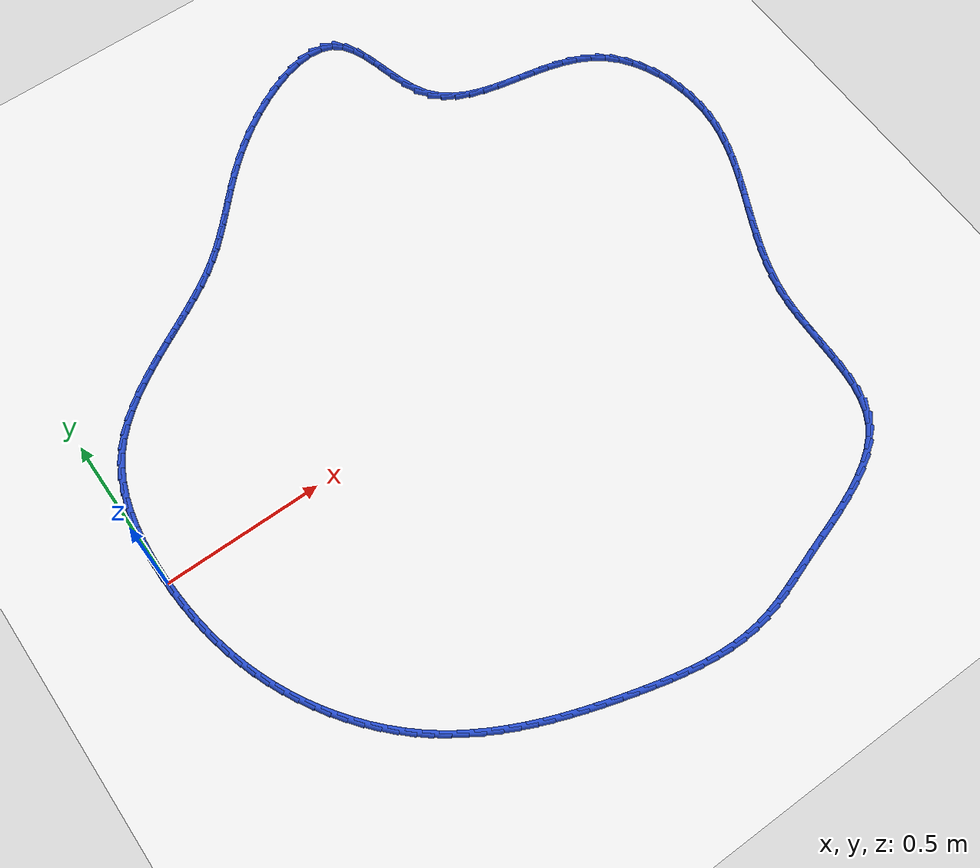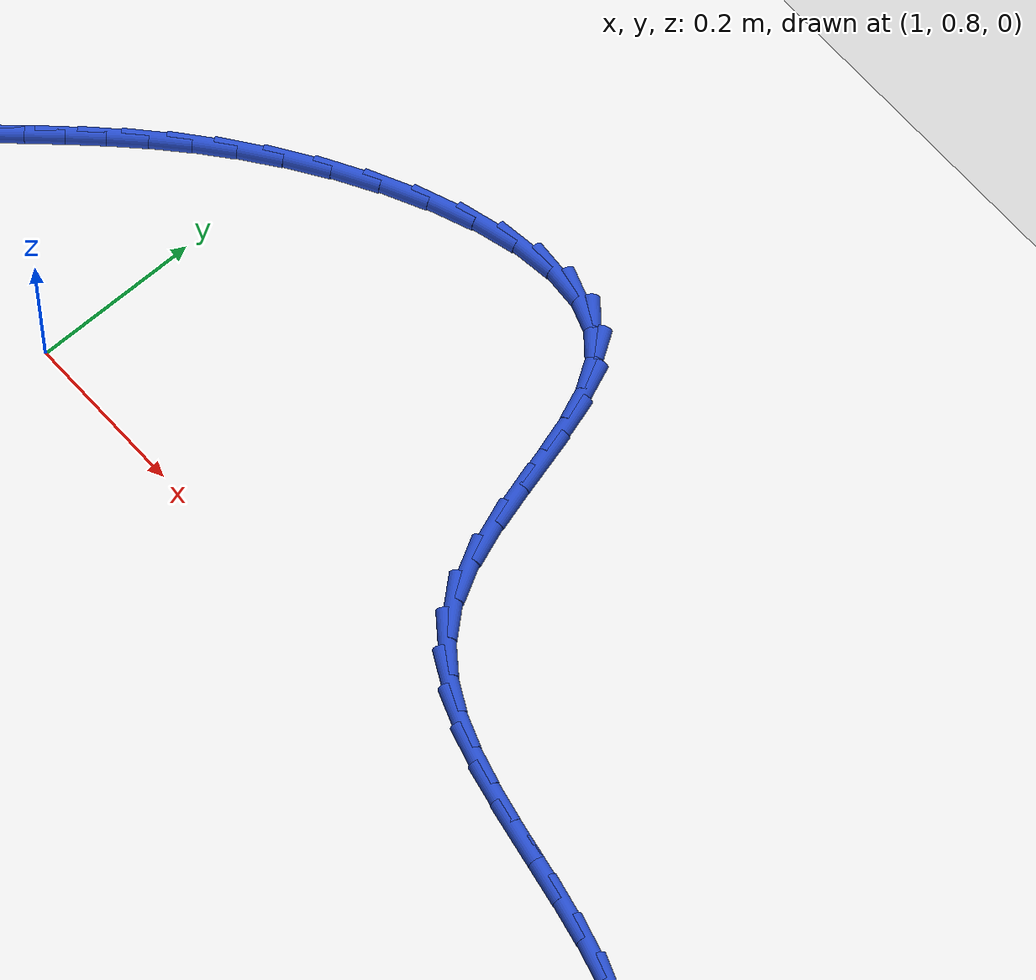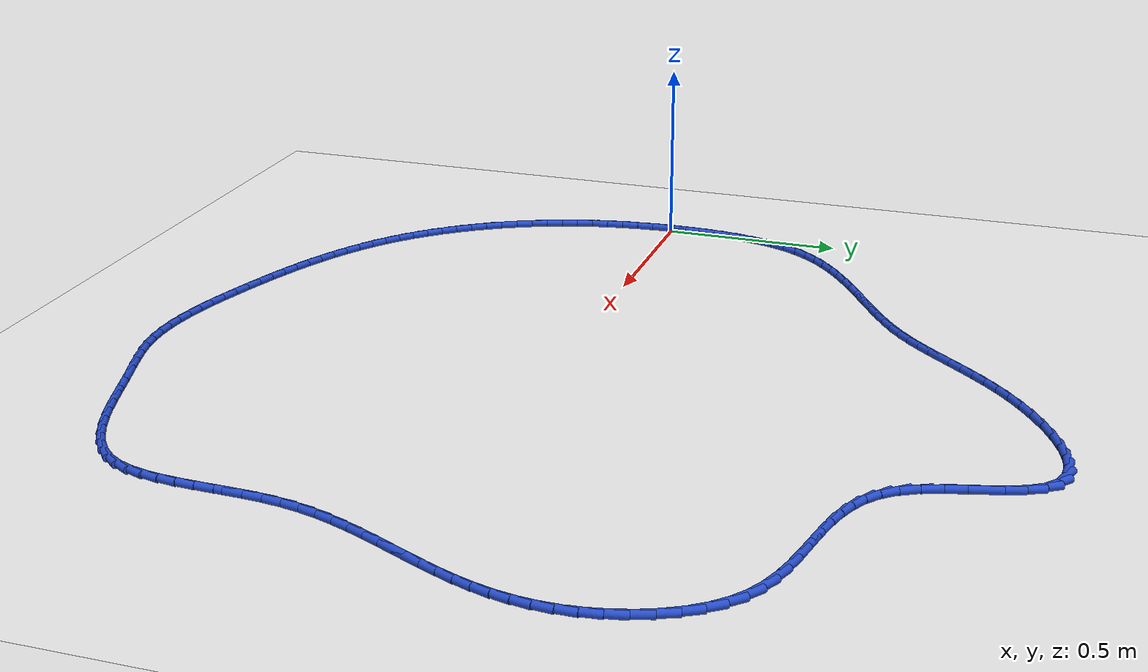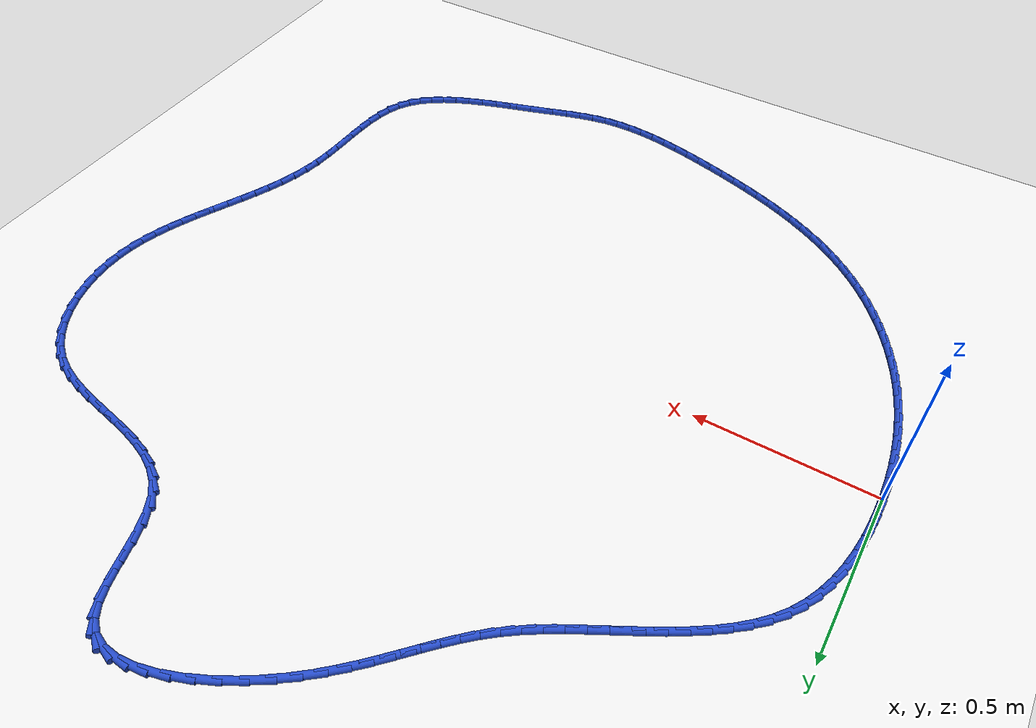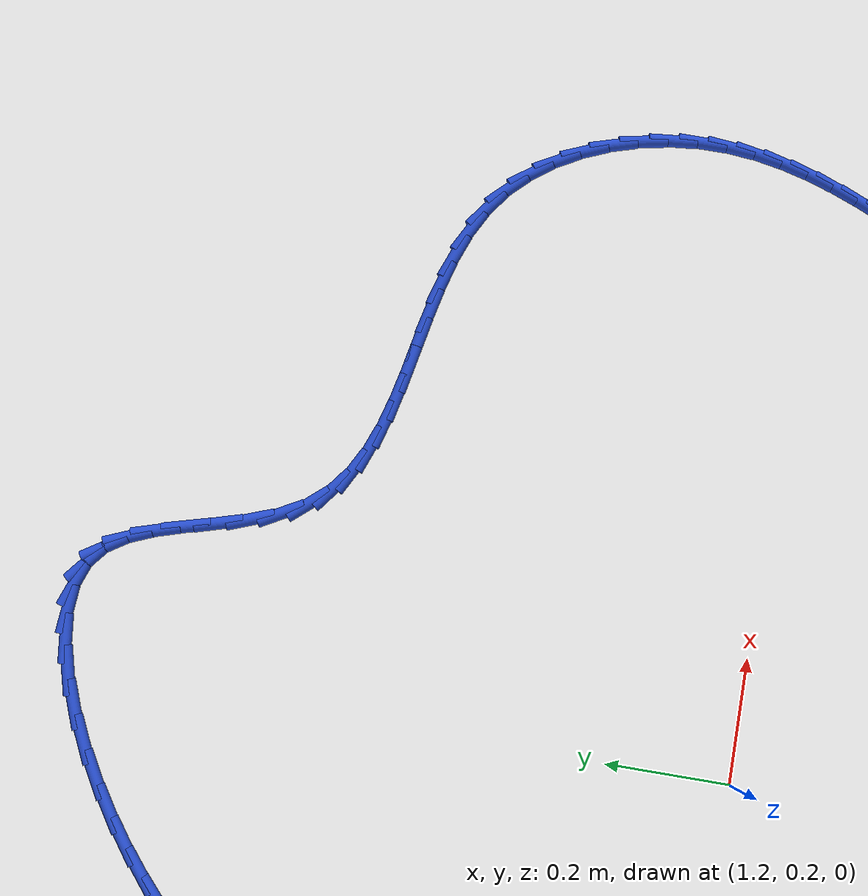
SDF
<sdf version="1.6">
 <world name="default">
  <light name="sun" type="directional">
   <pose>0 0 10 0 -0 0</pose>
   <diffuse>0.8 0.8 0.8 1</diffuse>
   <specular>0.2 0.2 0.2 1</specular>
   <attenuation>
    <range>1000</range>
    <constant>0.9</constant>
    <linear>0.01</linear>
    <quadratic>0.001</quadratic>
   </attenuation>
   <direction>-0.5 0.1 -0.9</direction>
  </light>
  <model name="ground_plane">
   <static>1</static>
   <link name="link">
    <collision name="collision">
     <geometry><plane><normal>0 0 1</normal><size>100 100</size></plane></geometry>
     <surface><friction><ode><mu>100</mu><mu2>50</mu2></ode></friction></surface>
    </collision>
    <visual name="visual">
     <cast_shadows>0</cast_shadows>
     <geometry><plane><normal>0 0 1</normal><size>100 100</size></plane></geometry>
     <material>
      <script><uri>file://media/materials/scripts/gazebo.material</uri><name>Gazebo/WhiteGlow</name></script>
     </material>
    </visual>
   </link>
  </model>
  <gravity>0 0 -9.8</gravity>
  <magnetic_field>6e-06 2.3e-05 -4.2e-05</magnetic_field>
  <atmosphere type="adiabatic"/>
  <physics name="default_physics" default="0" type="ode">
   <max_step_size>0.001</max_step_size>
   <real_time_factor>1</real_time_factor>
   <real_time_update_rate>1000</real_time_update_rate>
  </physics>
  <scene><ambient>0.4 0.4 0.4 1</ambient><background>0.7 0.7 0.7 1</background><shadows>1</shadows></scene>
  <spherical_coordinates>
   <surface_model>EARTH_WGS84</surface_model>
   <latitude_deg>0</latitude_deg>
   <longitude_deg>0</longitude_deg>
   <elevation>0</elevation>
   <heading_deg>0</heading_deg>
  </spherical_coordinates>
  <model name="line">
   <link name="link_0">
    <pose>6.071532165918825e-18 8.326672684688674e-17 0.01 0 1.57 -1.5597542882293989</pose>
    <collision name="collision">
     <geometry><cylinder><radius>0.01</radius><length>0.08</length></cylinder></geometry>
    </collision>
    <visual name="visual">
     <material>
      <script><name>Gazebo/Blue</name><uri>file://media/materials/scripts/gazebo.material</uri></script>
     </material>
     <geometry><cylinder><radius>0.01</radius><length>0.08</length></cylinder></geometry>
    </visual>
   </link>
   <link name="link_1">
    <pose>-0.0005402952393984356 0.04892876231369978 0.01 0 1.57 1.541204479486744</pose>
    <collision name="collision">
     <geometry><cylinder><radius>0.01</radius><length>0.08</length></cylinder></geometry>
    </collision>
    <visual name="visual">
     <material>
      <script><name>Gazebo/Blue</name><uri>file://media/materials/scripts/gazebo.material</uri></script>
     </material>
     <geometry><cylinder><radius>0.01</radius><length>0.08</length></cylinder></geometry>
    </visual>
   </link>
   <link name="link_2">
    <pose>0.000913420278070266 0.09803996341378214 0.01 0 1.57 1.4947157895868406</pose>
    <collision name="collision">
     <geometry><cylinder><radius>0.01</radius><length>0.08</length></cylinder></geometry>
    </collision>
    <visual name="visual">
     <material>
      <script><name>Gazebo/Blue</name><uri>file://media/materials/scripts/gazebo.material</uri></script>
     </material>
     <geometry><cylinder><radius>0.01</radius><length>0.08</length></cylinder></geometry>
    </visual>
   </link>
   <link name="link_3">
    <pose>0.004639800676113368 0.14692484278581508 0.01 0 1.57 1.4414148175023616</pose>
    <collision name="collision">
     <geometry><cylinder><radius>0.01</radius><length>0.08</length></cylinder></geometry>
    </collision>
    <visual name="visual">
     <material>
      <script><name>Gazebo/Blue</name><uri>file://media/materials/scripts/gazebo.material</uri></script>
     </material>
     <geometry><cylinder><radius>0.01</radius><length>0.08</length></cylinder></geometry>
    </visual>
   </link>
   <link name="link_4">
    <pose>0.010917500078438155 0.1951746399153666 0.01 0 1.57 1.3802033425470173</pose>
    <collision name="collision">
     <geometry><cylinder><radius>0.01</radius><length>0.08</length></cylinder></geometry>
    </collision>
    <visual name="visual">
     <material>
      <script><name>Gazebo/Blue</name><uri>file://media/materials/scripts/gazebo.material</uri></script>
     </material>
     <geometry><cylinder><radius>0.01</radius><length>0.08</length></cylinder></geometry>
    </visual>
   </link>
   <link name="link_5">
    <pose>0.020025172608751883 0.2423805942880045 0.01 0 1.57 1.3098795944967991</pose>
    <collision name="collision">
     <geometry><cylinder><radius>0.01</radius><length>0.08</length></cylinder></geometry>
    </collision>
    <visual name="visual">
     <material>
      <script><name>Gazebo/Blue</name><uri>file://media/materials/scripts/gazebo.material</uri></script>
     </material>
     <geometry><cylinder><radius>0.01</radius><length>0.08</length></cylinder></geometry>
    </visual>
   </link>
   <link name="link_6">
    <pose>0.03224147239076184 0.28813394538929676 0.01 0 1.57 1.2292305687645277</pose>
    <collision name="collision">
     <geometry><cylinder><radius>0.01</radius><length>0.08</length></cylinder></geometry>
    </collision>
    <visual name="visual">
     <material>
      <script><name>Gazebo/Blue</name><uri>file://media/materials/scripts/gazebo.material</uri></script>
     </material>
     <geometry><cylinder><radius>0.01</radius><length>0.08</length></cylinder></geometry>
    </visual>
   </link>
   <link name="link_7">
    <pose>0.047845053548175295 0.3320259327048114 0.01 0 1.57 1.137212159363858</pose>
    <collision name="collision">
     <geometry><cylinder><radius>0.01</radius><length>0.08</length></cylinder></geometry>
    </collision>
    <visual name="visual">
     <material>
      <script><name>Gazebo/Blue</name><uri>file://media/materials/scripts/gazebo.material</uri></script>
     </material>
     <geometry><cylinder><radius>0.01</radius><length>0.08</length></cylinder></geometry>
    </visual>
   </link>
   <link name="link_8">
    <pose>0.0671145702046995 0.37364779572011625 0.01 0 1.57 1.0332599340760333</pose>
    <collision name="collision">
     <geometry><cylinder><radius>0.01</radius><length>0.08</length></cylinder></geometry>
    </collision>
    <visual name="visual">
     <material>
      <script><name>Gazebo/Blue</name><uri>file://media/materials/scripts/gazebo.material</uri></script>
     </material>
     <geometry><cylinder><radius>0.01</radius><length>0.08</length></cylinder></geometry>
    </visual>
   </link>
   <link name="link_9">
    <pose>0.09032819974240336 0.41259123659162755 0.01 0 1.57 0.9236243283278152</pose>
    <collision name="collision">
     <geometry><cylinder><radius>0.01</radius><length>0.08</length></cylinder></geometry>
    </collision>
    <visual name="visual">
     <material>
      <script><name>Gazebo/Blue</name><uri>file://media/materials/scripts/gazebo.material</uri></script>
     </material>
     <geometry><cylinder><radius>0.01</radius><length>0.08</length></cylinder></geometry>
    </visual>
   </link>
   <link name="link_10">
    <pose>0.11756962563614366 0.4486367109929215 0.01 0 1.57 0.8249873401306519</pose>
    <collision name="collision">
     <geometry><cylinder><radius>0.01</radius><length>0.08</length></cylinder></geometry>
    </collision>
    <visual name="visual">
     <material>
      <script><name>Gazebo/Blue</name><uri>file://media/materials/scripts/gazebo.material</uri></script>
     </material>
     <geometry><cylinder><radius>0.01</radius><length>0.08</length></cylinder></geometry>
    </visual>
   </link>
   <link name="link_11">
    <pose>0.1484300012942756 0.4820426678863737 0.01 0 1.57 0.7409636124235105</pose>
    <collision name="collision">
     <geometry><cylinder><radius>0.01</radius><length>0.08</length></cylinder></geometry>
    </collision>
    <visual name="visual">
     <material>
      <script><name>Gazebo/Blue</name><uri>file://media/materials/scripts/gazebo.material</uri></script>
     </material>
     <geometry><cylinder><radius>0.01</radius><length>0.08</length></cylinder></geometry>
    </visual>
   </link>
   <link name="link_12">
    <pose>0.18242369566501554 0.5131420744396951 0.01 0 1.57 0.6716165635296051</pose>
    <collision name="collision">
     <geometry><cylinder><radius>0.01</radius><length>0.08</length></cylinder></geometry>
    </collision>
    <visual name="visual">
     <material>
      <script><name>Gazebo/Blue</name><uri>file://media/materials/scripts/gazebo.material</uri></script>
     </material>
     <geometry><cylinder><radius>0.01</radius><length>0.08</length></cylinder></geometry>
    </visual>
   </link>
   <link name="link_13">
    <pose>0.21906507769658012 0.5422678978205978 0.01 0 1.57 0.616287298810233</pose>
    <collision name="collision">
     <geometry><cylinder><radius>0.01</radius><length>0.08</length></cylinder></geometry>
    </collision>
    <visual name="visual">
     <material>
      <script><name>Gazebo/Blue</name><uri>file://media/materials/scripts/gazebo.material</uri></script>
     </material>
     <geometry><cylinder><radius>0.01</radius><length>0.08</length></cylinder></geometry>
    </visual>
   </link>
   <link name="link_14">
    <pose>0.25786851633718605 0.5697531051967937 0.01 0 1.57 0.5740384557072363</pose>
    <collision name="collision">
     <geometry><cylinder><radius>0.01</radius><length>0.08</length></cylinder></geometry>
    </collision>
    <visual name="visual">
     <material>
      <script><name>Gazebo/Blue</name><uri>file://media/materials/scripts/gazebo.material</uri></script>
     </material>
     <geometry><cylinder><radius>0.01</radius><length>0.08</length></cylinder></geometry>
    </visual>
   </link>
   <link name="link_15">
    <pose>0.2983483805350497 0.5959306637359943 0.01 0 1.57 0.5439495653624512</pose>
    <collision name="collision">
     <geometry><cylinder><radius>0.01</radius><length>0.08</length></cylinder></geometry>
    </collision>
    <visual name="visual">
     <material>
      <script><name>Gazebo/Blue</name><uri>file://media/materials/scripts/gazebo.material</uri></script>
     </material>
     <geometry><cylinder><radius>0.01</radius><length>0.08</length></cylinder></geometry>
    </visual>
   </link>
   <link name="link_16">
    <pose>0.34001903923838767 0.6211335406059114 0.01 0 1.57 0.5252868296294332</pose>
    <collision name="collision">
     <geometry><cylinder><radius>0.01</radius><length>0.08</length></cylinder></geometry>
    </collision>
    <visual name="visual">
     <material>
      <script><name>Gazebo/Blue</name><uri>file://media/materials/scripts/gazebo.material</uri></script>
     </material>
     <geometry><cylinder><radius>0.01</radius><length>0.08</length></cylinder></geometry>
    </visual>
   </link>
   <link name="link_17">
    <pose>0.38239486139541656 0.6456947029742568 0.01 0 1.57 0.5175910837712329</pose>
    <collision name="collision">
     <geometry><cylinder><radius>0.01</radius><length>0.08</length></cylinder></geometry>
    </collision>
    <visual name="visual">
     <material>
      <script><name>Gazebo/Blue</name><uri>file://media/materials/scripts/gazebo.material</uri></script>
     </material>
     <geometry><cylinder><radius>0.01</radius><length>0.08</length></cylinder></geometry>
    </visual>
   </link>
   <link name="link_18">
    <pose>0.42499021595435316 0.6699471180087422 0.01 0 1.57 0.5207205984611785</pose>
    <collision name="collision">
     <geometry><cylinder><radius>0.01</radius><length>0.08</length></cylinder></geometry>
    </collision>
    <visual name="visual">
     <material>
      <script><name>Gazebo/Blue</name><uri>file://media/materials/scripts/gazebo.material</uri></script>
     </material>
     <geometry><cylinder><radius>0.01</radius><length>0.08</length></cylinder></geometry>
    </visual>
   </link>
   <link name="link_19">
    <pose>0.4673194718634136 0.6942237528770792 0.01 0 1.57 0.5348711903887335</pose>
    <collision name="collision">
     <geometry><cylinder><radius>0.01</radius><length>0.08</length></cylinder></geometry>
    </collision>
    <visual name="visual">
     <material>
      <script><name>Gazebo/Blue</name><uri>file://media/materials/scripts/gazebo.material</uri></script>
     </material>
     <geometry><cylinder><radius>0.01</radius><length>0.08</length></cylinder></geometry>
    </visual>
   </link>
   <link name="link_20">
    <pose>0.5088969980708147 0.7188575747469796 0.01 0 1.57 0.5605821735108621</pose>
    <collision name="collision">
     <geometry><cylinder><radius>0.01</radius><length>0.08</length></cylinder></geometry>
    </collision>
    <visual name="visual">
     <material>
      <script><name>Gazebo/Blue</name><uri>file://media/materials/scripts/gazebo.material</uri></script>
     </material>
     <geometry><cylinder><radius>0.01</radius><length>0.08</length></cylinder></geometry>
    </visual>
   </link>
   <link name="link_21">
    <pose>0.549237163524773 0.7441815507861551 0.01 0 1.57 0.5987229923804348</pose>
    <collision name="collision">
     <geometry><cylinder><radius>0.01</radius><length>0.08</length></cylinder></geometry>
    </collision>
    <visual name="visual">
     <material>
      <script><name>Gazebo/Blue</name><uri>file://media/materials/scripts/gazebo.material</uri></script>
     </material>
     <geometry><cylinder><radius>0.01</radius><length>0.08</length></cylinder></geometry>
    </visual>
   </link>
   <link name="link_22">
    <pose>0.5878543371735052 0.7705286481623177 0.01 0 1.57 0.6504222927535331</pose>
    <collision name="collision">
     <geometry><cylinder><radius>0.01</radius><length>0.08</length></cylinder></geometry>
    </collision>
    <visual name="visual">
     <material>
      <script><name>Gazebo/Blue</name><uri>file://media/materials/scripts/gazebo.material</uri></script>
     </material>
     <geometry><cylinder><radius>0.01</radius><length>0.08</length></cylinder></geometry>
    </visual>
   </link>
   <link name="link_23">
    <pose>0.6242636686467243 0.798231450913832 0.01 0 1.57 0.7102466502169098</pose>
    <collision name="collision">
     <geometry><cylinder><radius>0.01</radius><length>0.08</length></cylinder></geometry>
    </collision>
    <visual name="visual">
     <material>
      <script><name>Gazebo/Blue</name><uri>file://media/materials/scripts/gazebo.material</uri></script>
     </material>
     <geometry><cylinder><radius>0.01</radius><length>0.08</length></cylinder></geometry>
    </visual>
   </link>
   <link name="link_24">
    <pose>0.6582736409104464 0.8274785860234535 0.01 0 1.57 0.7610161418452425</pose>
    <collision name="collision">
     <geometry><cylinder><radius>0.01</radius><length>0.08</length></cylinder></geometry>
    </collision>
    <visual name="visual">
     <material>
      <script><name>Gazebo/Blue</name><uri>file://media/materials/scripts/gazebo.material</uri></script>
     </material>
     <geometry><cylinder><radius>0.01</radius><length>0.08</length></cylinder></geometry>
    </visual>
   </link>
   <link name="link_25">
    <pose>0.6904251228997973 0.8580992527695683 0.01 0 1.57 0.7985035697229289</pose>
    <collision name="collision">
     <geometry><cylinder><radius>0.01</radius><length>0.08</length></cylinder></geometry>
    </collision>
    <visual name="visual">
     <material>
      <script><name>Gazebo/Blue</name><uri>file://media/materials/scripts/gazebo.material</uri></script>
     </material>
     <geometry><cylinder><radius>0.01</radius><length>0.08</length></cylinder></geometry>
    </visual>
   </link>
   <link name="link_26">
    <pose>0.7213714030949564 0.8898674791128302 0.01 0 1.57 0.821769163624296</pose>
    <collision name="collision">
     <geometry><cylinder><radius>0.01</radius><length>0.08</length></cylinder></geometry>
    </collision>
    <visual name="visual">
     <material>
      <script><name>Gazebo/Blue</name><uri>file://media/materials/scripts/gazebo.material</uri></script>
     </material>
     <geometry><cylinder><radius>0.01</radius><length>0.08</length></cylinder></geometry>
    </visual>
   </link>
   <link name="link_27">
    <pose>0.7517657699761022 0.9225572930138927 0.01 0 1.57 0.8306027006182115</pose>
    <collision name="collision">
     <geometry><cylinder><radius>0.01</radius><length>0.08</length></cylinder></geometry>
    </collision>
    <visual name="visual">
     <material>
      <script><name>Gazebo/Blue</name><uri>file://media/materials/scripts/gazebo.material</uri></script>
     </material>
     <geometry><cylinder><radius>0.01</radius><length>0.08</length></cylinder></geometry>
    </visual>
   </link>
   <link name="link_28">
    <pose>0.7822615120234139 0.9559427224334098 0.01 0 1.57 0.8253837216076464</pose>
    <collision name="collision">
     <geometry><cylinder><radius>0.01</radius><length>0.08</length></cylinder></geometry>
    </collision>
    <visual name="visual">
     <material>
      <script><name>Gazebo/Blue</name><uri>file://media/materials/scripts/gazebo.material</uri></script>
     </material>
     <geometry><cylinder><radius>0.01</radius><length>0.08</length></cylinder></geometry>
    </visual>
   </link>
   <link name="link_29">
    <pose>0.8135119177170703 0.9897977953320349 0.01 0 1.57 0.8069713445529281</pose>
    <collision name="collision">
     <geometry><cylinder><radius>0.01</radius><length>0.08</length></cylinder></geometry>
    </collision>
    <visual name="visual">
     <material>
      <script><name>Gazebo/Blue</name><uri>file://media/materials/scripts/gazebo.material</uri></script>
     </material>
     <geometry><cylinder><radius>0.01</radius><length>0.08</length></cylinder></geometry>
    </visual>
   </link>
   <link name="link_30">
    <pose>0.84617027553725 1.0238965396704214 0.01 0 1.57 0.7766361946108075</pose>
    <collision name="collision">
     <geometry><cylinder><radius>0.01</radius><length>0.08</length></cylinder></geometry>
    </collision>
    <visual name="visual">
     <material>
      <script><name>Gazebo/Blue</name><uri>file://media/materials/scripts/gazebo.material</uri></script>
     </material>
     <geometry><cylinder><radius>0.01</radius><length>0.08</length></cylinder></geometry>
    </visual>
   </link>
   <link name="link_31">
    <pose>0.8808898739641324 1.0580129834092231 0.01 0 1.57 0.7360152615232175</pose>
    <collision name="collision">
     <geometry><cylinder><radius>0.01</radius><length>0.08</length></cylinder></geometry>
    </collision>
    <visual name="visual">
     <material>
      <script><name>Gazebo/Blue</name><uri>file://media/materials/scripts/gazebo.material</uri></script>
     </material>
     <geometry><cylinder><radius>0.01</radius><length>0.08</length></cylinder></geometry>
    </visual>
   </link>
   <link name="link_32">
    <pose>0.9183240014778962 1.0919211545090939 0.01 0 1.57 0.6870569364966587</pose>
    <collision name="collision">
     <geometry><cylinder><radius>0.01</radius><length>0.08</length></cylinder></geometry>
    </collision>
    <visual name="visual">
     <material>
      <script><name>Gazebo/Blue</name><uri>file://media/materials/scripts/gazebo.material</uri></script>
     </material>
     <geometry><cylinder><radius>0.01</radius><length>0.08</length></cylinder></geometry>
    </visual>
   </link>
   <link name="link_33">
    <pose>0.9591259465587201 1.125395080930687 0.01 0 1.57 0.6322761132818642</pose>
    <collision name="collision">
     <geometry><cylinder><radius>0.01</radius><length>0.08</length></cylinder></geometry>
    </collision>
    <visual name="visual">
     <material>
      <script><name>Gazebo/Blue</name><uri>file://media/materials/scripts/gazebo.material</uri></script>
     </material>
     <geometry><cylinder><radius>0.01</radius><length>0.08</length></cylinder></geometry>
    </visual>
   </link>
   <link name="link_34">
    <pose>1.0038480545519186 1.1581587943908582 0.01 0 1.57 0.5759994394089678</pose>
    <collision name="collision">
     <geometry><cylinder><radius>0.01</radius><length>0.08</length></cylinder></geometry>
    </collision>
    <visual name="visual">
     <material>
      <script><name>Gazebo/Blue</name><uri>file://media/materials/scripts/gazebo.material</uri></script>
     </material>
     <geometry><cylinder><radius>0.01</radius><length>0.08</length></cylinder></geometry>
    </visual>
   </link>
   <link name="link_35">
    <pose>1.0519226545113907 1.1893815924223268 0.01 0 1.57 0.5167653526301275</pose>
    <collision name="collision">
     <geometry><cylinder><radius>0.01</radius><length>0.08</length></cylinder></geometry>
    </collision>
    <visual name="visual">
     <material>
      <script><name>Gazebo/Blue</name><uri>file://media/materials/scripts/gazebo.material</uri></script>
     </material>
     <geometry><cylinder><radius>0.01</radius><length>0.08</length></cylinder></geometry>
    </visual>
   </link>
   <link name="link_36">
    <pose>1.102084079459959 1.2178870612839696 0.01 0 1.57 0.4497486660711636</pose>
    <collision name="collision">
     <geometry><cylinder><radius>0.01</radius><length>0.08</length></cylinder></geometry>
    </collision>
    <visual name="visual">
     <material>
      <script><name>Gazebo/Blue</name><uri>file://media/materials/scripts/gazebo.material</uri></script>
     </material>
     <geometry><cylinder><radius>0.01</radius><length>0.08</length></cylinder></geometry>
    </visual>
   </link>
   <link name="link_37">
    <pose>1.1530560858600418 1.2424935487576403 0.01 0 1.57 0.3689032916469637</pose>
    <collision name="collision">
     <geometry><cylinder><radius>0.01</radius><length>0.08</length></cylinder></geometry>
    </collision>
    <visual name="visual">
     <material>
      <script><name>Gazebo/Blue</name><uri>file://media/materials/scripts/gazebo.material</uri></script>
     </material>
     <geometry><cylinder><radius>0.01</radius><length>0.08</length></cylinder></geometry>
    </visual>
   </link>
   <link name="link_38">
    <pose>1.2035624301740597 1.2620194026251952 0.01 0 1.57 0.26556814103729826</pose>
    <collision name="collision">
     <geometry><cylinder><radius>0.01</radius><length>0.08</length></cylinder></geometry>
    </collision>
    <visual name="visual">
     <material>
      <script><name>Gazebo/Blue</name><uri>file://media/materials/scripts/gazebo.material</uri></script>
     </material>
     <geometry><cylinder><radius>0.01</radius><length>0.08</length></cylinder></geometry>
    </visual>
   </link>
   <link name="link_39">
    <pose>1.252326868864432 1.275282970668489 0.01 0 1.57 0.12653565919637141</pose>
    <collision name="collision">
     <geometry><cylinder><radius>0.01</radius><length>0.08</length></cylinder></geometry>
    </collision>
    <visual name="visual">
     <material>
      <script><name>Gazebo/Blue</name><uri>file://media/materials/scripts/gazebo.material</uri></script>
     </material>
     <geometry><cylinder><radius>0.01</radius><length>0.08</length></cylinder></geometry>
    </visual>
   </link>
   <link name="link_40">
    <pose>1.2980731583935783 1.2811026006693764 0.01 0 1.57 -0.06758885342199733</pose>
    <collision name="collision">
     <geometry><cylinder><radius>0.01</radius><length>0.08</length></cylinder></geometry>
    </collision>
    <visual name="visual">
     <material>
      <script><name>Gazebo/Blue</name><uri>file://media/materials/scripts/gazebo.material</uri></script>
     </material>
     <geometry><cylinder><radius>0.01</radius><length>0.08</length></cylinder></geometry>
    </visual>
   </link>
   <link name="link_41">
    <pose>1.3395250552239184 1.2782966404097134 0.01 0 1.57 -0.3380338043413268</pose>
    <collision name="collision">
     <geometry><cylinder><radius>0.01</radius><length>0.08</length></cylinder></geometry>
    </collision>
    <visual name="visual">
     <material>
      <script><name>Gazebo/Blue</name><uri>file://media/materials/scripts/gazebo.material</uri></script>
     </material>
     <geometry><cylinder><radius>0.01</radius><length>0.08</length></cylinder></geometry>
    </visual>
   </link>
   <link name="link_42">
    <pose>1.375406315817873 1.2656834376713553 0.01 0 1.57 -0.6812646831049045</pose>
    <collision name="collision">
     <geometry><cylinder><radius>0.01</radius><length>0.08</length></cylinder></geometry>
    </collision>
    <visual name="visual">
     <material>
      <script><name>Gazebo/Blue</name><uri>file://media/materials/scripts/gazebo.material</uri></script>
     </material>
     <geometry><cylinder><radius>0.01</radius><length>0.08</length></cylinder></geometry>
    </visual>
   </link>
   <link name="link_43">
    <pose>1.404471682256628 1.242118540138018 0.01 0 1.57 -0.9909428610644206</pose>
    <collision name="collision">
     <geometry><cylinder><radius>0.01</radius><length>0.08</length></cylinder></geometry>
    </collision>
    <visual name="visual">
     <material>
      <script><name>Gazebo/Blue</name><uri>file://media/materials/scripts/gazebo.material</uri></script>
     </material>
     <geometry><cylinder><radius>0.01</radius><length>0.08</length></cylinder></geometry>
    </visual>
   </link>
   <link name="link_44">
    <pose>1.4267927477637337 1.2080384461153526 0.01 0 1.57 -1.17768620382468</pose>
    <collision name="collision">
     <geometry><cylinder><radius>0.01</radius><length>0.08</length></cylinder></geometry>
    </collision>
    <visual name="visual">
     <material>
      <script><name>Gazebo/Blue</name><uri>file://media/materials/scripts/gazebo.material</uri></script>
     </material>
     <geometry><cylinder><radius>0.01</radius><length>0.08</length></cylinder></geometry>
    </visual>
   </link>
   <link name="link_45">
    <pose>1.4442196929021902 1.166014943669567 0.01 0 1.57 -1.272831639590615</pose>
    <collision name="collision">
     <geometry><cylinder><radius>0.01</radius><length>0.08</length></cylinder></geometry>
    </collision>
    <visual name="visual">
     <material>
      <script><name>Gazebo/Blue</name><uri>file://media/materials/scripts/gazebo.material</uri></script>
     </material>
     <geometry><cylinder><radius>0.01</radius><length>0.08</length></cylinder></geometry>
    </visual>
   </link>
   <link name="link_46">
    <pose>1.4587286544277087 1.1187710380506517 0.01 0 1.57 -1.3045198656573231</pose>
    <collision name="collision">
     <geometry><cylinder><radius>0.01</radius><length>0.08</length></cylinder></geometry>
    </collision>
    <visual name="visual">
     <material>
      <script><name>Gazebo/Blue</name><uri>file://media/materials/scripts/gazebo.material</uri></script>
     </material>
     <geometry><cylinder><radius>0.01</radius><length>0.08</length></cylinder></geometry>
    </visual>
   </link>
   <link name="link_47">
    <pose>1.472295769096004 1.0690297345085982 0.01 0 1.57 -1.284039359393539</pose>
    <collision name="collision">
     <geometry><cylinder><radius>0.01</radius><length>0.08</length></cylinder></geometry>
    </collision>
    <visual name="visual">
     <material>
      <script><name>Gazebo/Blue</name><uri>file://media/materials/scripts/gazebo.material</uri></script>
     </material>
     <geometry><cylinder><radius>0.01</radius><length>0.08</length></cylinder></geometry>
    </visual>
   </link>
   <link name="link_48">
    <pose>1.486897173662789 1.019514038293397 0.01 0 1.57 -1.209220123331976</pose>
    <collision name="collision">
     <geometry><cylinder><radius>0.01</radius><length>0.08</length></cylinder></geometry>
    </collision>
    <visual name="visual">
     <material>
      <script><name>Gazebo/Blue</name><uri>file://media/materials/scripts/gazebo.material</uri></script>
     </material>
     <geometry><cylinder><radius>0.01</radius><length>0.08</length></cylinder></geometry>
    </visual>
   </link>
   <link name="link_49">
    <pose>1.5045090048837781 0.9729469546550393 0.01 0 1.57 -1.0659769933967027</pose>
    <collision name="collision">
     <geometry><cylinder><radius>0.01</radius><length>0.08</length></cylinder></geometry>
    </collision>
    <visual name="visual">
     <material>
      <script><name>Gazebo/Blue</name><uri>file://media/materials/scripts/gazebo.material</uri></script>
     </material>
     <geometry><cylinder><radius>0.01</radius><length>0.08</length></cylinder></geometry>
    </visual>
   </link>
   <link name="link_50">
    <pose>1.5271071053052683 0.932051092990625 0.01 0 1.57 -0.8556877142055355</pose>
    <collision name="collision">
     <geometry><cylinder><radius>0.01</radius><length>0.08</length></cylinder></geometry>
    </collision>
    <visual name="visual">
     <material>
      <script><name>Gazebo/Blue</name><uri>file://media/materials/scripts/gazebo.material</uri></script>
     </material>
     <geometry><cylinder><radius>0.01</radius><length>0.08</length></cylinder></geometry>
    </visual>
   </link>
   <link name="link_51">
    <pose>1.5560522328969857 0.8987214786895014 0.01 0 1.57 -0.6505263449974029</pose>
    <collision name="collision">
     <geometry><cylinder><radius>0.01</radius><length>0.08</length></cylinder></geometry>
    </collision>
    <visual name="visual">
     <material>
      <script><name>Gazebo/Blue</name><uri>file://media/materials/scripts/gazebo.material</uri></script>
     </material>
     <geometry><cylinder><radius>0.01</radius><length>0.08</length></cylinder></geometry>
    </visual>
   </link>
   <link name="link_52">
    <pose>1.5907940190582714 0.8722817545268398 0.01 0 1.57 -0.4819558796842431</pose>
    <collision name="collision">
     <geometry><cylinder><radius>0.01</radius><length>0.08</length></cylinder></geometry>
    </collision>
    <visual name="visual">
     <material>
      <script><name>Gazebo/Blue</name><uri>file://media/materials/scripts/gazebo.material</uri></script>
     </material>
     <geometry><cylinder><radius>0.01</radius><length>0.08</length></cylinder></geometry>
    </visual>
   </link>
   <link name="link_53">
    <pose>1.6304120031551108 0.8515576118417504 0.01 0 1.57 -0.35560250245032154</pose>
    <collision name="collision">
     <geometry><cylinder><radius>0.01</radius><length>0.08</length></cylinder></geometry>
    </collision>
    <visual name="visual">
     <material>
      <script><name>Gazebo/Blue</name><uri>file://media/materials/scripts/gazebo.material</uri></script>
     </material>
     <geometry><cylinder><radius>0.01</radius><length>0.08</length></cylinder></geometry>
    </visual>
   </link>
   <link name="link_54">
    <pose>1.6739857245534877 0.8353747419733429 0.01 0 1.57 -0.26833491926444314</pose>
    <collision name="collision">
     <geometry><cylinder><radius>0.01</radius><length>0.08</length></cylinder></geometry>
    </collision>
    <visual name="visual">
     <material>
      <script><name>Gazebo/Blue</name><uri>file://media/materials/scripts/gazebo.material</uri></script>
     </material>
     <geometry><cylinder><radius>0.01</radius><length>0.08</length></cylinder></geometry>
    </visual>
   </link>
   <link name="link_55">
    <pose>1.720594722619386 0.8225588362607277 0.01 0 1.57 -0.2146704180902622</pose>
    <collision name="collision">
     <geometry><cylinder><radius>0.01</radius><length>0.08</length></cylinder></geometry>
    </collision>
    <visual name="visual">
     <material>
      <script><name>Gazebo/Blue</name><uri>file://media/materials/scripts/gazebo.material</uri></script>
     </material>
     <geometry><cylinder><radius>0.01</radius><length>0.08</length></cylinder></geometry>
    </visual>
   </link>
   <link name="link_56">
    <pose>1.7693185367187916 0.8119355860430147 0.01 0 1.57 -0.19008981165271416</pose>
    <collision name="collision">
     <geometry><cylinder><radius>0.01</radius><length>0.08</length></cylinder></geometry>
    </collision>
    <visual name="visual">
     <material>
      <script><name>Gazebo/Blue</name><uri>file://media/materials/scripts/gazebo.material</uri></script>
     </material>
     <geometry><cylinder><radius>0.01</radius><length>0.08</length></cylinder></geometry>
    </visual>
   </link>
   <link name="link_57">
    <pose>1.8192367062176866 0.8023306826593134 0.01 0 1.57 -0.19207291950445188</pose>
    <collision name="collision">
     <geometry><cylinder><radius>0.01</radius><length>0.08</length></cylinder></geometry>
    </collision>
    <visual name="visual">
     <material>
      <script><name>Gazebo/Blue</name><uri>file://media/materials/scripts/gazebo.material</uri></script>
     </material>
     <geometry><cylinder><radius>0.01</radius><length>0.08</length></cylinder></geometry>
    </visual>
   </link>
   <link name="link_58">
    <pose>1.8694287704820582 0.7925698174487343 0.01 0 1.57 -0.22022681116998813</pose>
    <collision name="collision">
     <geometry><cylinder><radius>0.01</radius><length>0.08</length></cylinder></geometry>
    </collision>
    <visual name="visual">
     <material>
      <script><name>Gazebo/Blue</name><uri>file://media/materials/scripts/gazebo.material</uri></script>
     </material>
     <geometry><cylinder><radius>0.01</radius><length>0.08</length></cylinder></geometry>
    </visual>
   </link>
   <link name="link_59">
    <pose>1.918974268877889 0.7814786817503874 0.01 0 1.57 -0.2761320272393438</pose>
    <collision name="collision">
     <geometry><cylinder><radius>0.01</radius><length>0.08</length></cylinder></geometry>
    </collision>
    <visual name="visual">
     <material>
      <script><name>Gazebo/Blue</name><uri>file://media/materials/scripts/gazebo.material</uri></script>
     </material>
     <geometry><cylinder><radius>0.01</radius><length>0.08</length></cylinder></geometry>
    </visual>
   </link>
   <link name="link_60">
    <pose>1.966952740771164 0.7678829669033825 0.01 0 1.57 -0.362917032537193</pose>
    <collision name="collision">
     <geometry><cylinder><radius>0.01</radius><length>0.08</length></cylinder></geometry>
    </collision>
    <visual name="visual">
     <material>
      <script><name>Gazebo/Blue</name><uri>file://media/materials/scripts/gazebo.material</uri></script>
     </material>
     <geometry><cylinder><radius>0.01</radius><length>0.08</length></cylinder></geometry>
    </visual>
   </link>
   <link name="link_61">
    <pose>2.0124437255278673 0.7506083642468296 0.01 0 1.57 -0.48408395912542634</pose>
    <collision name="collision">
     <geometry><cylinder><radius>0.01</radius><length>0.08</length></cylinder></geometry>
    </collision>
    <visual name="visual">
     <material>
      <script><name>Gazebo/Blue</name><uri>file://media/materials/scripts/gazebo.material</uri></script>
     </material>
     <geometry><cylinder><radius>0.01</radius><length>0.08</length></cylinder></geometry>
    </visual>
   </link>
   <link name="link_62">
    <pose>2.0545267625139836 0.7284805651198384 0.01 0 1.57 -0.6388505090146699</pose>
    <collision name="collision">
     <geometry><cylinder><radius>0.01</radius><length>0.08</length></cylinder></geometry>
    </collision>
    <visual name="visual">
     <material>
      <script><name>Gazebo/Blue</name><uri>file://media/materials/scripts/gazebo.material</uri></script>
     </material>
     <geometry><cylinder><radius>0.01</radius><length>0.08</length></cylinder></geometry>
    </visual>
   </link>
   <link name="link_63">
    <pose>2.092317512462558 0.700411158965178 0.01 0 1.57 -0.7973936949464182</pose>
    <collision name="collision">
     <geometry><cylinder><radius>0.01</radius><length>0.08</length></cylinder></geometry>
    </collision>
    <visual name="visual">
     <material>
      <script><name>Gazebo/Blue</name><uri>file://media/materials/scripts/gazebo.material</uri></script>
     </material>
     <geometry><cylinder><radius>0.01</radius><length>0.08</length></cylinder></geometry>
    </visual>
   </link>
   <link name="link_64">
    <pose>2.1254293294177824 0.6664952704877162 0.01 0 1.57 -0.9388658881188598</pose>
    <collision name="collision">
     <geometry><cylinder><radius>0.01</radius><length>0.08</length></cylinder></geometry>
    </collision>
    <visual name="visual">
     <material>
      <script><name>Gazebo/Blue</name><uri>file://media/materials/scripts/gazebo.material</uri></script>
     </material>
     <geometry><cylinder><radius>0.01</radius><length>0.08</length></cylinder></geometry>
    </visual>
   </link>
   <link name="link_65">
    <pose>2.1538379235372873 0.6276897222051803 0.01 0 1.57 -1.064475225966758</pose>
    <collision name="collision">
     <geometry><cylinder><radius>0.01</radius><length>0.08</length></cylinder></geometry>
    </collision>
    <visual name="visual">
     <material>
      <script><name>Gazebo/Blue</name><uri>file://media/materials/scripts/gazebo.material</uri></script>
     </material>
     <geometry><cylinder><radius>0.01</radius><length>0.08</length></cylinder></geometry>
    </visual>
   </link>
   <link name="link_66">
    <pose>2.177527201439901 0.5849708281587657 0.01 0 1.57 -1.1773017465877713</pose>
    <collision name="collision">
     <geometry><cylinder><radius>0.01</radius><length>0.08</length></cylinder></geometry>
    </collision>
    <visual name="visual">
     <material>
      <script><name>Gazebo/Blue</name><uri>file://media/materials/scripts/gazebo.material</uri></script>
     </material>
     <geometry><cylinder><radius>0.01</radius><length>0.08</length></cylinder></geometry>
    </visual>
   </link>
   <link name="link_67">
    <pose>2.196481069744455 0.5393149023896676 0.01 0 1.57 -1.2809322820455342</pose>
    <collision name="collision">
     <geometry><cylinder><radius>0.01</radius><length>0.08</length></cylinder></geometry>
    </collision>
    <visual name="visual">
     <material>
      <script><name>Gazebo/Blue</name><uri>file://media/materials/scripts/gazebo.material</uri></script>
     </material>
     <geometry><cylinder><radius>0.01</radius><length>0.08</length></cylinder></geometry>
    </visual>
   </link>
   <link name="link_68">
    <pose>2.210683435069776 0.49169825893908226 0.01 0 1.57 -1.37905433625036</pose>
    <collision name="collision">
     <geometry><cylinder><radius>0.01</radius><length>0.08</length></cylinder></geometry>
    </collision>
    <visual name="visual">
     <material>
      <script><name>Gazebo/Blue</name><uri>file://media/materials/scripts/gazebo.material</uri></script>
     </material>
     <geometry><cylinder><radius>0.01</radius><length>0.08</length></cylinder></geometry>
    </visual>
   </link>
   <link name="link_69">
    <pose>2.220118204034697 0.4430972118482046 0.01 0 1.57 -1.4754035051091712</pose>
    <collision name="collision">
     <geometry><cylinder><radius>0.01</radius><length>0.08</length></cylinder></geometry>
    </collision>
    <visual name="visual">
     <material>
      <script><name>Gazebo/Blue</name><uri>file://media/materials/scripts/gazebo.material</uri></script>
     </material>
     <geometry><cylinder><radius>0.01</radius><length>0.08</length></cylinder></geometry>
    </visual>
   </link>
   <link name="link_70">
    <pose>2.224769283258044 0.39448807515823003 0.01 0 1.57 1.5681327462050796</pose>
    <collision name="collision">
     <geometry><cylinder><radius>0.01</radius><length>0.08</length></cylinder></geometry>
    </collision>
    <visual name="visual">
     <material>
      <script><name>Gazebo/Blue</name><uri>file://media/materials/scripts/gazebo.material</uri></script>
     </material>
     <geometry><cylinder><radius>0.01</radius><length>0.08</length></cylinder></geometry>
    </visual>
   </link>
   <link name="link_71">
    <pose>2.224642269766901 0.3468029436267451 0.01 0 1.57 1.4723205233510952</pose>
    <collision name="collision">
     <geometry><cylinder><radius>0.01</radius><length>0.08</length></cylinder></geometry>
    </collision>
    <visual name="visual">
     <material>
      <script><name>Gazebo/Blue</name><uri>file://media/materials/scripts/gazebo.material</uri></script>
     </material>
     <geometry><cylinder><radius>0.01</radius><length>0.08</length></cylinder></geometry>
    </visual>
   </link>
   <link name="link_72">
    <pose>2.2200522413773234 0.3003429871057611 0.01 0 1.57 1.3855771424489935</pose>
    <collision name="collision">
     <geometry><cylinder><radius>0.01</radius><length>0.08</length></cylinder></geometry>
    </collision>
    <visual name="visual">
     <material>
      <script><name>Gazebo/Blue</name><uri>file://media/materials/scripts/gazebo.material</uri></script>
     </material>
     <geometry><cylinder><radius>0.01</radius><length>0.08</length></cylinder></geometry>
    </visual>
   </link>
   <link name="link_73">
    <pose>2.2115450341750384 0.25493893868774525 0.01 0 1.57 1.3102207452271597</pose>
    <collision name="collision">
     <geometry><cylinder><radius>0.01</radius><length>0.08</length></cylinder></geometry>
    </collision>
    <visual name="visual">
     <material>
      <script><name>Gazebo/Blue</name><uri>file://media/materials/scripts/gazebo.material</uri></script>
     </material>
     <geometry><cylinder><radius>0.01</radius><length>0.08</length></cylinder></geometry>
    </visual>
   </link>
   <link name="link_74">
    <pose>2.1996720036892596 0.21041027921790162 0.01 0 1.57 1.2474813245618075</pose>
    <collision name="collision">
     <geometry><cylinder><radius>0.01</radius><length>0.08</length></cylinder></geometry>
    </collision>
    <visual name="visual">
     <material>
      <script><name>Gazebo/Blue</name><uri>file://media/materials/scripts/gazebo.material</uri></script>
     </material>
     <geometry><cylinder><radius>0.01</radius><length>0.08</length></cylinder></geometry>
    </visual>
   </link>
   <link name="link_75">
    <pose>2.1849845054492048 0.1665764895414343 0.01 0 1.57 1.197818101572983</pose>
    <collision name="collision">
     <geometry><cylinder><radius>0.01</radius><length>0.08</length></cylinder></geometry>
    </collision>
    <visual name="visual">
     <material>
      <script><name>Gazebo/Blue</name><uri>file://media/materials/scripts/gazebo.material</uri></script>
     </material>
     <geometry><cylinder><radius>0.01</radius><length>0.08</length></cylinder></geometry>
    </visual>
   </link>
   <link name="link_76">
    <pose>2.168033894984086 0.12325705050354711 0.01 0 1.57 1.161197901994755</pose>
    <collision name="collision">
     <geometry><cylinder><radius>0.01</radius><length>0.08</length></cylinder></geometry>
    </collision>
    <visual name="visual">
     <material>
      <script><name>Gazebo/Blue</name><uri>file://media/materials/scripts/gazebo.material</uri></script>
     </material>
     <geometry><cylinder><radius>0.01</radius><length>0.08</length></cylinder></geometry>
    </visual>
   </link>
   <link name="link_77">
    <pose>2.149371527823119 0.08027144294944447 0.01 0 1.57 1.1373493947982103</pose>
    <collision name="collision">
     <geometry><cylinder><radius>0.01</radius><length>0.08</length></cylinder></geometry>
    </collision>
    <visual name="visual">
     <material>
      <script><name>Gazebo/Blue</name><uri>file://media/materials/scripts/gazebo.material</uri></script>
     </material>
     <geometry><cylinder><radius>0.01</radius><length>0.08</length></cylinder></geometry>
    </visual>
   </link>
   <link name="link_78">
    <pose>2.1295487594955205 0.03743914772433124 0.01 0 1.57 1.1259487516540034</pose>
    <collision name="collision">
     <geometry><cylinder><radius>0.01</radius><length>0.08</length></cylinder></geometry>
    </collision>
    <visual name="visual">
     <material>
      <script><name>Gazebo/Blue</name><uri>file://media/materials/scripts/gazebo.material</uri></script>
     </material>
     <geometry><cylinder><radius>0.01</radius><length>0.08</length></cylinder></geometry>
    </visual>
   </link>
   <link name="link_79">
    <pose>2.1091169455305026 -0.005420354326589889 0.01 0 1.57 1.126731117023253</pose>
    <collision name="collision">
     <geometry><cylinder><radius>0.01</radius><length>0.08</length></cylinder></geometry>
    </collision>
    <visual name="visual">
     <material>
      <script><name>Gazebo/Blue</name><uri>file://media/materials/scripts/gazebo.material</uri></script>
     </material>
     <geometry><cylinder><radius>0.01</radius><length>0.08</length></cylinder></geometry>
    </visual>
   </link>
   <link name="link_80">
    <pose>2.0886274414572825 -0.04848758235811345 0.01 0 1.57 1.1395375372983945</pose>
    <collision name="collision">
     <geometry><cylinder><radius>0.01</radius><length>0.08</length></cylinder></geometry>
    </collision>
    <visual name="visual">
     <material>
      <script><name>Gazebo/Blue</name><uri>file://media/materials/scripts/gazebo.material</uri></script>
     </material>
     <geometry><cylinder><radius>0.01</radius><length>0.08</length></cylinder></geometry>
    </visual>
   </link>
   <link name="link_81">
    <pose>2.0686316028050733 -0.09194305552503665 0.01 0 1.57 1.1643073467445144</pose>
    <collision name="collision">
     <geometry><cylinder><radius>0.01</radius><length>0.08</length></cylinder></geometry>
    </collision>
    <visual name="visual">
     <material>
      <script><name>Gazebo/Blue</name><uri>file://media/materials/scripts/gazebo.material</uri></script>
     </material>
     <geometry><cylinder><radius>0.01</radius><length>0.08</length></cylinder></geometry>
    </visual>
   </link>
   <link name="link_82">
    <pose>2.049680785103091 -0.13596729298215476 0.01 0 1.57 1.2010207366002288</pose>
    <collision name="collision">
     <geometry><cylinder><radius>0.01</radius><length>0.08</length></cylinder></geometry>
    </collision>
    <visual name="visual">
     <material>
      <script><name>Gazebo/Blue</name><uri>file://media/materials/scripts/gazebo.material</uri></script>
     </material>
     <geometry><cylinder><radius>0.01</radius><length>0.08</length></cylinder></geometry>
    </visual>
   </link>
   <link name="link_83">
    <pose>2.03232634388055 -0.18074081388426289 0.01 0 1.57 1.2495919755594584</pose>
    <collision name="collision">
     <geometry><cylinder><radius>0.01</radius><length>0.08</length></cylinder></geometry>
    </collision>
    <visual name="visual">
     <material>
      <script><name>Gazebo/Blue</name><uri>file://media/materials/scripts/gazebo.material</uri></script>
     </material>
     <geometry><cylinder><radius>0.01</radius><length>0.08</length></cylinder></geometry>
    </visual>
   </link>
   <link name="link_84">
    <pose>2.017119634666665 -0.22644413738615832 0.01 0 1.57 1.3097157015065861</pose>
    <collision name="collision">
     <geometry><cylinder><radius>0.01</radius><length>0.08</length></cylinder></geometry>
    </collision>
    <visual name="visual">
     <material>
      <script><name>Gazebo/Blue</name><uri>file://media/materials/scripts/gazebo.material</uri></script>
     </material>
     <geometry><cylinder><radius>0.01</radius><length>0.08</length></cylinder></geometry>
    </visual>
   </link>
   <link name="link_85">
    <pose>2.004612012990652 -0.2732577826426355 0.01 0 1.57 1.3806765601021136</pose>
    <collision name="collision">
     <geometry><cylinder><radius>0.01</radius><length>0.08</length></cylinder></geometry>
    </collision>
    <visual name="visual">
     <material>
      <script><name>Gazebo/Blue</name><uri>file://media/materials/scripts/gazebo.material</uri></script>
     </material>
     <geometry><cylinder><radius>0.01</radius><length>0.08</length></cylinder></geometry>
    </visual>
   </link>
   <link name="link_86">
    <pose>1.9953546116338436 -0.32136216407954804 0.01 0 1.57 1.4537378015769884</pose>
    <collision name="collision">
     <geometry><cylinder><radius>0.01</radius><length>0.08</length></cylinder></geometry>
    </collision>
    <visual name="visual">
     <material>
      <script><name>Gazebo/Blue</name><uri>file://media/materials/scripts/gazebo.material</uri></script>
     </material>
     <geometry><cylinder><radius>0.01</radius><length>0.08</length></cylinder></geometry>
    </visual>
   </link>
   <link name="link_87">
    <pose>1.9895443070122918 -0.3707711360869299 0.01 0 1.57 1.5063964218680699</pose>
    <collision name="collision">
     <geometry><cylinder><radius>0.01</radius><length>0.08</length></cylinder></geometry>
    </collision>
    <visual name="visual">
     <material>
      <script><name>Gazebo/Blue</name><uri>file://media/materials/scripts/gazebo.material</uri></script>
     </material>
     <geometry><cylinder><radius>0.01</radius><length>0.08</length></cylinder></geometry>
    </visual>
   </link>
   <link name="link_88">
    <pose>1.9863054618118219 -0.4209942913313108 0.01 0 1.57 1.5362184551931717</pose>
    <collision name="collision">
     <geometry><cylinder><radius>0.01</radius><length>0.08</length></cylinder></geometry>
    </collision>
    <visual name="visual">
     <material>
      <script><name>Gazebo/Blue</name><uri>file://media/materials/scripts/gazebo.material</uri></script>
     </material>
     <geometry><cylinder><radius>0.01</radius><length>0.08</length></cylinder></geometry>
    </visual>
   </link>
   <link name="link_89">
    <pose>1.9845602480158848 -0.4714461588644795 0.01 0 1.57 1.5442648252155826</pose>
    <collision name="collision">
     <geometry><cylinder><radius>0.01</radius><length>0.08</length></cylinder></geometry>
    </collision>
    <visual name="visual">
     <material>
      <script><name>Gazebo/Blue</name><uri>file://media/materials/scripts/gazebo.material</uri></script>
     </material>
     <geometry><cylinder><radius>0.01</radius><length>0.08</length></cylinder></geometry>
    </visual>
   </link>
   <link name="link_90">
    <pose>1.9832308376079324 -0.5215412677382232 0.01 0 1.57 1.5303033484049997</pose>
    <collision name="collision">
     <geometry><cylinder><radius>0.01</radius><length>0.08</length></cylinder></geometry>
    </collision>
    <visual name="visual">
     <material>
      <script><name>Gazebo/Blue</name><uri>file://media/materials/scripts/gazebo.material</uri></script>
     </material>
     <geometry><cylinder><radius>0.01</radius><length>0.08</length></cylinder></geometry>
    </visual>
   </link>
   <link name="link_91">
    <pose>1.9812394025714148 -0.5706941470043279 0.01 0 1.57 1.4926090893344475</pose>
    <collision name="collision">
     <geometry><cylinder><radius>0.01</radius><length>0.08</length></cylinder></geometry>
    </collision>
    <visual name="visual">
     <material>
      <script><name>Gazebo/Blue</name><uri>file://media/materials/scripts/gazebo.material</uri></script>
     </material>
     <geometry><cylinder><radius>0.01</radius><length>0.08</length></cylinder></geometry>
    </visual>
   </link>
   <link name="link_92">
    <pose>1.9775081148897848 -0.6183193257145835 0.01 0 1.57 1.4278819313989901</pose>
    <collision name="collision">
     <geometry><cylinder><radius>0.01</radius><length>0.08</length></cylinder></geometry>
    </collision>
    <visual name="visual">
     <material>
      <script><name>Gazebo/Blue</name><uri>file://media/materials/scripts/gazebo.material</uri></script>
     </material>
     <geometry><cylinder><radius>0.01</radius><length>0.08</length></cylinder></geometry>
    </visual>
   </link>
   <link name="link_93">
    <pose>1.9709591465464906 -0.6638313329207748 0.01 0 1.57 1.3315163825500467</pose>
    <collision name="collision">
     <geometry><cylinder><radius>0.01</radius><length>0.08</length></cylinder></geometry>
    </collision>
    <visual name="visual">
     <material>
      <script><name>Gazebo/Blue</name><uri>file://media/materials/scripts/gazebo.material</uri></script>
     </material>
     <geometry><cylinder><radius>0.01</radius><length>0.08</length></cylinder></geometry>
    </visual>
   </link>
   <link name="link_94">
    <pose>1.9605146695249858 -0.706644697674692 0.01 0 1.57 1.1989093873212857</pose>
    <collision name="collision">
     <geometry><cylinder><radius>0.01</radius><length>0.08</length></cylinder></geometry>
    </collision>
    <visual name="visual">
     <material>
      <script><name>Gazebo/Blue</name><uri>file://media/materials/scripts/gazebo.material</uri></script>
     </material>
     <geometry><cylinder><radius>0.01</radius><length>0.08</length></cylinder></geometry>
    </visual>
   </link>
   <link name="link_95">
    <pose>1.9450968558087198 -0.746173949028121 0.01 0 1.57 1.0294599945411178</pose>
    <collision name="collision">
     <geometry><cylinder><radius>0.01</radius><length>0.08</length></cylinder></geometry>
    </collision>
    <visual name="visual">
     <material>
      <script><name>Gazebo/Blue</name><uri>file://media/materials/scripts/gazebo.material</uri></script>
     </material>
     <geometry><cylinder><radius>0.01</radius><length>0.08</length></cylinder></geometry>
    </visual>
   </link>
   <link name="link_96">
    <pose>1.923649501951573 -0.7818453673206515 0.01 0 1.57 0.8516620677811731</pose>
    <collision name="collision">
     <geometry><cylinder><radius>0.01</radius><length>0.08</length></cylinder></geometry>
    </collision>
    <visual name="visual">
     <material>
      <script><name>Gazebo/Blue</name><uri>file://media/materials/scripts/gazebo.material</uri></script>
     </material>
     <geometry><cylinder><radius>0.01</radius><length>0.08</length></cylinder></geometry>
    </visual>
   </link>
   <link name="link_97">
    <pose>1.895916945658604 -0.8135202653239123 0.01 0 1.57 0.7014278966095441</pose>
    <collision name="collision">
     <geometry><cylinder><radius>0.01</radius><length>0.08</length></cylinder></geometry>
    </collision>
    <visual name="visual">
     <material>
      <script><name>Gazebo/Blue</name><uri>file://media/materials/scripts/gazebo.material</uri></script>
     </material>
     <geometry><cylinder><radius>0.01</radius><length>0.08</length></cylinder></geometry>
    </visual>
   </link>
   <link name="link_98">
    <pose>1.8626608267356737 -0.8416127811157331 0.01 0 1.57 0.5817469343441324</pose>
    <collision name="collision">
     <geometry><cylinder><radius>0.01</radius><length>0.08</length></cylinder></geometry>
    </collision>
    <visual name="visual">
     <material>
      <script><name>Gazebo/Blue</name><uri>file://media/materials/scripts/gazebo.material</uri></script>
     </material>
     <geometry><cylinder><radius>0.01</radius><length>0.08</length></cylinder></geometry>
    </visual>
   </link>
   <link name="link_99">
    <pose>1.8247085435567925 -0.866572787488879 0.01 0 1.57 0.4894510212537441</pose>
    <collision name="collision">
     <geometry><cylinder><radius>0.01</radius><length>0.08</length></cylinder></geometry>
    </collision>
    <visual name="visual">
     <material>
      <script><name>Gazebo/Blue</name><uri>file://media/materials/scripts/gazebo.material</uri></script>
     </material>
     <geometry><cylinder><radius>0.01</radius><length>0.08</length></cylinder></geometry>
    </visual>
   </link>
   <link name="link_100">
    <pose>1.7828874944959732 -0.8888501572361142 0.01 0 1.57 0.4201910721192538</pose>
    <collision name="collision">
     <geometry><cylinder><radius>0.01</radius><length>0.08</length></cylinder></geometry>
    </collision>
    <visual name="visual">
     <material>
      <script><name>Gazebo/Blue</name><uri>file://media/materials/scripts/gazebo.material</uri></script>
     </material>
     <geometry><cylinder><radius>0.01</radius><length>0.08</length></cylinder></geometry>
    </visual>
   </link>
   <link name="link_101">
    <pose>1.738025077927228 -0.908894763150203 0.01 0 1.57 0.3700465122258667</pose>
    <collision name="collision">
     <geometry><cylinder><radius>0.01</radius><length>0.08</length></cylinder></geometry>
    </collision>
    <visual name="visual">
     <material>
      <script><name>Gazebo/Blue</name><uri>file://media/materials/scripts/gazebo.material</uri></script>
     </material>
     <geometry><cylinder><radius>0.01</radius><length>0.08</length></cylinder></geometry>
    </visual>
   </link>
   <link name="link_102">
    <pose>1.690948692224568 -0.9271564780239107 0.01 0 1.57 0.3360618508742253</pose>
    <collision name="collision">
     <geometry><cylinder><radius>0.01</radius><length>0.08</length></cylinder></geometry>
    </collision>
    <visual name="visual">
     <material>
      <script><name>Gazebo/Blue</name><uri>file://media/materials/scripts/gazebo.material</uri></script>
     </material>
     <geometry><cylinder><radius>0.01</radius><length>0.08</length></cylinder></geometry>
    </visual>
   </link>
   <link name="link_103">
    <pose>1.6424857357620055 -0.9440851746500015 0.01 0 1.57 0.31632197173776677</pose>
    <collision name="collision">
     <geometry><cylinder><radius>0.01</radius><length>0.08</length></cylinder></geometry>
    </collision>
    <visual name="visual">
     <material>
      <script><name>Gazebo/Blue</name><uri>file://media/materials/scripts/gazebo.material</uri></script>
     </material>
     <geometry><cylinder><radius>0.01</radius><length>0.08</length></cylinder></geometry>
    </visual>
   </link>
   <link name="link_104">
    <pose>1.5934636069135544 -0.96013072582124 0.01 0 1.57 0.30990814692698104</pose>
    <collision name="collision">
     <geometry><cylinder><radius>0.01</radius><length>0.08</length></cylinder></geometry>
    </collision>
    <visual name="visual">
     <material>
      <script><name>Gazebo/Blue</name><uri>file://media/materials/scripts/gazebo.material</uri></script>
     </material>
     <geometry><cylinder><radius>0.01</radius><length>0.08</length></cylinder></geometry>
    </visual>
   </link>
   <link name="link_105">
    <pose>1.5447097040532245 -0.9757430043303912 0.01 0 1.57 0.3166155469952428</pose>
    <collision name="collision">
     <geometry><cylinder><radius>0.01</radius><length>0.08</length></cylinder></geometry>
    </collision>
    <visual name="visual">
     <material>
      <script><name>Gazebo/Blue</name><uri>file://media/materials/scripts/gazebo.material</uri></script>
     </material>
     <geometry><cylinder><radius>0.01</radius><length>0.08</length></cylinder></geometry>
    </visual>
   </link>
   <link name="link_106">
    <pose>1.4970406149158635 -0.9913611840413539 0.01 0 1.57 0.3245641332559445</pose>
    <collision name="collision">
     <geometry><cylinder><radius>0.01</radius><length>0.08</length></cylinder></geometry>
    </collision>
    <visual name="visual">
     <material>
      <script><name>Gazebo/Blue</name><uri>file://media/materials/scripts/gazebo.material</uri></script>
     </material>
     <geometry><cylinder><radius>0.01</radius><length>0.08</length></cylinder></geometry>
    </visual>
   </link>
   <link name="link_107">
    <pose>1.4507721122703883 -1.0069287989568516 0.01 0 1.57 0.3154102349154724</pose>
    <collision name="collision">
     <geometry><cylinder><radius>0.01</radius><length>0.08</length></cylinder></geometry>
    </collision>
    <visual name="visual">
     <material>
      <script><name>Gazebo/Blue</name><uri>file://media/materials/scripts/gazebo.material</uri></script>
     </material>
     <geometry><cylinder><radius>0.01</radius><length>0.08</length></cylinder></geometry>
    </visual>
   </link>
   <link name="link_108">
    <pose>1.4055185297306805 -1.021695192152662 0.01 0 1.57 0.2865145292667186</pose>
    <collision name="collision">
     <geometry><cylinder><radius>0.01</radius><length>0.08</length></cylinder></geometry>
    </collision>
    <visual name="visual">
     <material>
      <script><name>Gazebo/Blue</name><uri>file://media/materials/scripts/gazebo.material</uri></script>
     </material>
     <geometry><cylinder><radius>0.01</radius><length>0.08</length></cylinder></geometry>
    </visual>
   </link>
   <link name="link_109">
    <pose>1.3608418323408615 -1.0348578792784444 0.01 0 1.57 0.23697567218254945</pose>
    <collision name="collision">
     <geometry><cylinder><radius>0.01</radius><length>0.08</length></cylinder></geometry>
    </collision>
    <visual name="visual">
     <material>
      <script><name>Gazebo/Blue</name><uri>file://media/materials/scripts/gazebo.material</uri></script>
     </material>
     <geometry><cylinder><radius>0.01</radius><length>0.08</length></cylinder></geometry>
    </visual>
   </link>
   <link name="link_110">
    <pose>1.316303985145051 -1.045614375983858 0.01 0 1.57 0.16677964045662463</pose>
    <collision name="collision">
     <geometry><cylinder><radius>0.01</radius><length>0.08</length></cylinder></geometry>
    </collision>
    <visual name="visual">
     <material>
      <script><name>Gazebo/Blue</name><uri>file://media/materials/scripts/gazebo.material</uri></script>
     </material>
     <geometry><cylinder><radius>0.01</radius><length>0.08</length></cylinder></geometry>
    </visual>
   </link>
   <link name="link_111">
    <pose>1.2714670366838945 -1.0531623799524858 0.01 0 1.57 0.08342344863393857</pose>
    <collision name="collision">
     <geometry><cylinder><radius>0.01</radius><length>0.08</length></cylinder></geometry>
    </collision>
    <visual name="visual">
     <material>
      <script><name>Gazebo/Blue</name><uri>file://media/materials/scripts/gazebo.material</uri></script>
     </material>
     <geometry><cylinder><radius>0.01</radius><length>0.08</length></cylinder></geometry>
    </visual>
   </link>
   <link name="link_112">
    <pose>1.2260138859670624 -1.0569630595374513 0.01 0 1.57 0.006617679635156792</pose>
    <collision name="collision">
     <geometry><cylinder><radius>0.01</radius><length>0.08</length></cylinder></geometry>
    </collision>
    <visual name="visual">
     <material>
      <script><name>Gazebo/Blue</name><uri>file://media/materials/scripts/gazebo.material</uri></script>
     </material>
     <geometry><cylinder><radius>0.01</radius><length>0.08</length></cylinder></geometry>
    </visual>
   </link>
   <link name="link_113">
    <pose>1.1799898189328326 -1.0572676365147864 0.01 0 1.57 -0.06001207576289978</pose>
    <collision name="collision">
     <geometry><cylinder><radius>0.01</radius><length>0.08</length></cylinder></geometry>
    </collision>
    <visual name="visual">
     <material>
      <script><name>Gazebo/Blue</name><uri>file://media/materials/scripts/gazebo.material</uri></script>
     </material>
     <geometry><cylinder><radius>0.01</radius><length>0.08</length></cylinder></geometry>
    </visual>
   </link>
   <link name="link_114">
    <pose>1.1335077620031517 -1.0544747982323448 0.01 0 1.57 -0.11673997232816248</pose>
    <collision name="collision">
     <geometry><cylinder><radius>0.01</radius><length>0.08</length></cylinder></geometry>
    </collision>
    <visual name="visual">
     <material>
      <script><name>Gazebo/Blue</name><uri>file://media/materials/scripts/gazebo.material</uri></script>
     </material>
     <geometry><cylinder><radius>0.01</radius><length>0.08</length></cylinder></geometry>
    </visual>
   </link>
   <link name="link_115">
    <pose>1.0866806415999646 -1.0489832320379817 0.01 0 1.57 -0.16408157479082341</pose>
    <collision name="collision">
     <geometry><cylinder><radius>0.01</radius><length>0.08</length></cylinder></geometry>
    </collision>
    <visual name="visual">
     <material>
      <script><name>Gazebo/Blue</name><uri>file://media/materials/scripts/gazebo.material</uri></script>
     </material>
     <geometry><cylinder><radius>0.01</radius><length>0.08</length></cylinder></geometry>
    </visual>
   </link>
   <link name="link_116">
    <pose>1.039621384145217 -1.0411916252795508 0.01 0 1.57 -0.2026333327278535</pose>
    <collision name="collision">
     <geometry><cylinder><radius>0.01</radius><length>0.08</length></cylinder></geometry>
    </collision>
    <visual name="visual">
     <material>
      <script><name>Gazebo/Blue</name><uri>file://media/materials/scripts/gazebo.material</uri></script>
     </material>
     <geometry><cylinder><radius>0.01</radius><length>0.08</length></cylinder></geometry>
    </visual>
   </link>
   <link name="link_117">
    <pose>0.9924429160608571 -1.0314986653049076 0.01 0 1.57 -0.23296406980638998</pose>
    <collision name="collision">
     <geometry><cylinder><radius>0.01</radius><length>0.08</length></cylinder></geometry>
    </collision>
    <visual name="visual">
     <material>
      <script><name>Gazebo/Blue</name><uri>file://media/materials/scripts/gazebo.material</uri></script>
     </material>
     <geometry><cylinder><radius>0.01</radius><length>0.08</length></cylinder></geometry>
    </visual>
   </link>
   <link name="link_118">
    <pose>0.945258163768828 -1.0203030394619057 0.01 0 1.57 -0.2555474623899086</pose>
    <collision name="collision">
     <geometry><cylinder><radius>0.01</radius><length>0.08</length></cylinder></geometry>
    </collision>
    <visual name="visual">
     <material>
      <script><name>Gazebo/Blue</name><uri>file://media/materials/scripts/gazebo.material</uri></script>
     </material>
     <geometry><cylinder><radius>0.01</radius><length>0.08</length></cylinder></geometry>
    </visual>
   </link>
   <link name="link_119">
    <pose>0.8981800536910772 -1.0080034350984 0.01 0 1.57 -0.2712168360851853</pose>
    <collision name="collision">
     <geometry><cylinder><radius>0.01</radius><length>0.08</length></cylinder></geometry>
    </collision>
    <visual name="visual">
     <material>
      <script><name>Gazebo/Blue</name><uri>file://media/materials/scripts/gazebo.material</uri></script>
     </material>
     <geometry><cylinder><radius>0.01</radius><length>0.08</length></cylinder></geometry>
    </visual>
   </link>
   <link name="link_120">
    <pose>0.8513207522990911 -0.9949733339397069 0.01 0 1.57 -0.2860091408012626</pose>
    <collision name="collision">
     <geometry><cylinder><radius>0.01</radius><length>0.08</length></cylinder></geometry>
    </collision>
    <visual name="visual">
     <material>
      <script><name>Gazebo/Blue</name><uri>file://media/materials/scripts/gazebo.material</uri></script>
     </material>
     <geometry><cylinder><radius>0.01</radius><length>0.08</length></cylinder></geometry>
    </visual>
   </link>
   <link name="link_121">
    <pose>0.8047834355938411 -0.981288026686066 0.01 0 1.57 -0.30383685628598345</pose>
    <collision name="collision">
     <geometry><cylinder><radius>0.01</radius><length>0.08</length></cylinder></geometry>
    </collision>
    <visual name="visual">
     <material>
      <script><name>Gazebo/Blue</name><uri>file://media/materials/scripts/gazebo.material</uri></script>
     </material>
     <geometry><cylinder><radius>0.01</radius><length>0.08</length></cylinder></geometry>
    </visual>
   </link>
   <link name="link_122">
    <pose>0.7586654043056431 -0.9668279362634021 0.01 0 1.57 -0.32485176671512855</pose>
    <collision name="collision">
     <geometry><cylinder><radius>0.01</radius><length>0.08</length></cylinder></geometry>
    </collision>
    <visual name="visual">
     <material>
      <script><name>Gazebo/Blue</name><uri>file://media/materials/scripts/gazebo.material</uri></script>
     </material>
     <geometry><cylinder><radius>0.01</radius><length>0.08</length></cylinder></geometry>
    </visual>
   </link>
   <link name="link_123">
    <pose>0.7130638578197797 -0.9514701242408662 0.01 0 1.57 -0.34914886011278234</pose>
    <collision name="collision">
     <geometry><cylinder><radius>0.01</radius><length>0.08</length></cylinder></geometry>
    </collision>
    <visual name="visual">
     <material>
      <script><name>Gazebo/Blue</name><uri>file://media/materials/scripts/gazebo.material</uri></script>
     </material>
     <geometry><cylinder><radius>0.01</radius><length>0.08</length></cylinder></geometry>
    </visual>
   </link>
   <link name="link_124">
    <pose>0.6680759955215345 -0.9350916521876084 0.01 0 1.57 -0.37682660419285013</pose>
    <collision name="collision">
     <geometry><cylinder><radius>0.01</radius><length>0.08</length></cylinder></geometry>
    </collision>
    <visual name="visual">
     <material>
      <script><name>Gazebo/Blue</name><uri>file://media/materials/scripts/gazebo.material</uri></script>
     </material>
     <geometry><cylinder><radius>0.01</radius><length>0.08</length></cylinder></geometry>
    </visual>
   </link>
   <link name="link_125">
    <pose>0.623799016796192 -0.9175695816727798 0.01 0 1.57 -0.40797945272046254</pose>
    <collision name="collision">
     <geometry><cylinder><radius>0.01</radius><length>0.08</length></cylinder></geometry>
    </collision>
    <visual name="visual">
     <material>
      <script><name>Gazebo/Blue</name><uri>file://media/materials/scripts/gazebo.material</uri></script>
     </material>
     <geometry><cylinder><radius>0.01</radius><length>0.08</length></cylinder></geometry>
    </visual>
   </link>
   <link name="link_126">
    <pose>0.5803301210290339 -0.8987809742655303 0.01 0 1.57 -0.4426883171662665</pose>
    <collision name="collision">
     <geometry><cylinder><radius>0.01</radius><length>0.08</length></cylinder></geometry>
    </collision>
    <visual name="visual">
     <material>
      <script><name>Gazebo/Blue</name><uri>file://media/materials/scripts/gazebo.material</uri></script>
     </material>
     <geometry><cylinder><radius>0.01</radius><length>0.08</length></cylinder></geometry>
    </visual>
   </link>
   <link name="link_127">
    <pose>0.5377665076053448 -0.8786028915350108 0.01 0 1.57 -0.48100883896922186</pose>
    <collision name="collision">
     <geometry><cylinder><radius>0.01</radius><length>0.08</length></cylinder></geometry>
    </collision>
    <visual name="visual">
     <material>
      <script><name>Gazebo/Blue</name><uri>file://media/materials/scripts/gazebo.material</uri></script>
     </material>
     <geometry><cylinder><radius>0.01</radius><length>0.08</length></cylinder></geometry>
    </visual>
   </link>
   <link name="link_128">
    <pose>0.4962053759104069 -0.8569123950503713 0.01 0 1.57 -0.5229575446463163</pose>
    <collision name="collision">
     <geometry><cylinder><radius>0.01</radius><length>0.08</length></cylinder></geometry>
    </collision>
    <visual name="visual">
     <material>
      <script><name>Gazebo/Blue</name><uri>file://media/materials/scripts/gazebo.material</uri></script>
     </material>
     <geometry><cylinder><radius>0.01</radius><length>0.08</length></cylinder></geometry>
    </visual>
   </link>
   <link name="link_129">
    <pose>0.4557439253295041 -0.833586546380762 0.01 0 1.57 -0.5684963644926296</pose>
    <collision name="collision">
     <geometry><cylinder><radius>0.01</radius><length>0.08</length></cylinder></geometry>
    </collision>
    <visual name="visual">
     <material>
      <script><name>Gazebo/Blue</name><uri>file://media/materials/scripts/gazebo.material</uri></script>
     </material>
     <geometry><cylinder><radius>0.01</radius><length>0.08</length></cylinder></geometry>
    </visual>
   </link>
   <link name="link_130">
    <pose>0.4164793552479208 -0.8085024070953347 0.01 0 1.57 -0.6175165490645745</pose>
    <collision name="collision">
     <geometry><cylinder><radius>0.01</radius><length>0.08</length></cylinder></geometry>
    </collision>
    <visual name="visual">
     <material>
      <script><name>Gazebo/Blue</name><uri>file://media/materials/scripts/gazebo.material</uri></script>
     </material>
     <geometry><cylinder><radius>0.01</radius><length>0.08</length></cylinder></geometry>
    </visual>
   </link>
   <link name="link_131">
    <pose>0.37850886505093856 -0.7815370387632383 0.01 0 1.57 -0.6698236741678875</pose>
    <collision name="collision">
     <geometry><cylinder><radius>0.01</radius><length>0.08</length></cylinder></geometry>
    </collision>
    <visual name="visual">
     <material>
      <script><name>Gazebo/Blue</name><uri>file://media/materials/scripts/gazebo.material</uri></script>
     </material>
     <geometry><cylinder><radius>0.01</radius><length>0.08</length></cylinder></geometry>
    </visual>
   </link>
   <link name="link_132">
    <pose>0.34192965412384224 -0.7525675029536245 0.01 0 1.57 -0.7248565198020125</pose>
    <collision name="collision">
     <geometry><cylinder><radius>0.01</radius><length>0.08</length></cylinder></geometry>
    </collision>
    <visual name="visual">
     <material>
      <script><name>Gazebo/Blue</name><uri>file://media/materials/scripts/gazebo.material</uri></script>
     </material>
     <geometry><cylinder><radius>0.01</radius><length>0.08</length></cylinder></geometry>
    </visual>
   </link>
   <link name="link_133">
    <pose>0.3068379455068249 -0.721486877967123 0.01 0 1.57 -0.7795255132491349</pose>
    <collision name="collision">
     <geometry><cylinder><radius>0.01</radius><length>0.08</length></cylinder></geometry>
    </collision>
    <visual name="visual">
     <material>
      <script><name>Gazebo/Blue</name><uri>file://media/materials/scripts/gazebo.material</uri></script>
     </material>
     <geometry><cylinder><radius>0.01</radius><length>0.08</length></cylinder></geometry>
    </visual>
   </link>
   <link name="link_134">
    <pose>0.27331950288826096 -0.6883598255244492 0.01 0 1.57 -0.8323041004937256</pose>
    <collision name="collision">
     <geometry><cylinder><radius>0.01</radius><length>0.08</length></cylinder></geometry>
    </collision>
    <visual name="visual">
     <material>
      <script><name>Gazebo/Blue</name><uri>file://media/materials/scripts/gazebo.material</uri></script>
     </material>
     <geometry><cylinder><radius>0.01</radius><length>0.08</length></cylinder></geometry>
    </visual>
   </link>
   <link name="link_135">
    <pose>0.24145374216295723 -0.6533551415363639 0.01 0 1.57 -0.8834924357110876</pose>
    <collision name="collision">
     <geometry><cylinder><radius>0.01</radius><length>0.08</length></cylinder></geometry>
    </collision>
    <visual name="visual">
     <material>
      <script><name>Gazebo/Blue</name><uri>file://media/materials/scripts/gazebo.material</uri></script>
     </material>
     <geometry><cylinder><radius>0.01</radius><length>0.08</length></cylinder></geometry>
    </visual>
   </link>
   <link name="link_136">
    <pose>0.21131999003754312 -0.6166430850264983 0.01 0 1.57 -0.9334214595181501</pose>
    <collision name="collision">
     <geometry><cylinder><radius>0.01</radius><length>0.08</length></cylinder></geometry>
    </collision>
    <visual name="visual">
     <material>
      <script><name>Gazebo/Blue</name><uri>file://media/materials/scripts/gazebo.material</uri></script>
     </material>
     <geometry><cylinder><radius>0.01</radius><length>0.08</length></cylinder></geometry>
    </visual>
   </link>
   <link name="link_137">
    <pose>0.18299757321864968 -0.5783939150184861 0.01 0 1.57 -0.9824255742372701</pose>
    <collision name="collision">
     <geometry><cylinder><radius>0.01</radius><length>0.08</length></cylinder></geometry>
    </collision>
    <visual name="visual">
     <material>
      <script><name>Gazebo/Blue</name><uri>file://media/materials/scripts/gazebo.material</uri></script>
     </material>
     <geometry><cylinder><radius>0.01</radius><length>0.08</length></cylinder></geometry>
    </visual>
   </link>
   <link name="link_138">
    <pose>0.15656581841290756 -0.5387778905359604 0.01 0 1.57 -1.0308418836739686</pose>
    <collision name="collision">
     <geometry><cylinder><radius>0.01</radius><length>0.08</length></cylinder></geometry>
    </collision>
    <visual name="visual">
     <material>
      <script><name>Gazebo/Blue</name><uri>file://media/materials/scripts/gazebo.material</uri></script>
     </material>
     <geometry><cylinder><radius>0.01</radius><length>0.08</length></cylinder></geometry>
    </visual>
   </link>
   <link name="link_139">
    <pose>0.1321040523269465 -0.4979652706025527 0.01 0 1.57 -1.0790108474797664</pose>
    <collision name="collision">
     <geometry><cylinder><radius>0.01</radius><length>0.08</length></cylinder></geometry>
    </collision>
    <visual name="visual">
     <material>
      <script><name>Gazebo/Blue</name><uri>file://media/materials/scripts/gazebo.material</uri></script>
     </material>
     <geometry><cylinder><radius>0.01</radius><length>0.08</length></cylinder></geometry>
    </visual>
   </link>
   <link name="link_140">
    <pose>0.10969160166739757 -0.45612631424189665 0.01 0 1.57 -1.127277906303158</pose>
    <collision name="collision">
     <geometry><cylinder><radius>0.01</radius><length>0.08</length></cylinder></geometry>
    </collision>
    <visual name="visual">
     <material>
      <script><name>Gazebo/Blue</name><uri>file://media/materials/scripts/gazebo.material</uri></script>
     </material>
     <geometry><cylinder><radius>0.01</radius><length>0.08</length></cylinder></geometry>
    </visual>
   </link>
   <link name="link_141">
    <pose>0.08940779314089048 -0.413431280477624 0.01 0 1.57 -1.1758602136028224</pose>
    <collision name="collision">
     <geometry><cylinder><radius>0.01</radius><length>0.08</length></cylinder></geometry>
    </collision>
    <visual name="visual">
     <material>
      <script><name>Gazebo/Blue</name><uri>file://media/materials/scripts/gazebo.material</uri></script>
     </material>
     <geometry><cylinder><radius>0.01</radius><length>0.08</length></cylinder></geometry>
    </visual>
   </link>
   <link name="link_142">
    <pose>0.07131824845288552 -0.37003409763462763 0.01 0 1.57 -1.224045237836199</pose>
    <collision name="collision">
     <geometry><cylinder><radius>0.01</radius><length>0.08</length></cylinder></geometry>
    </collision>
    <visual name="visual">
     <material>
      <script><name>Gazebo/Blue</name><uri>file://media/materials/scripts/gazebo.material</uri></script>
     </material>
     <geometry><cylinder><radius>0.01</radius><length>0.08</length></cylinder></geometry>
    </visual>
   </link>
   <link name="link_143">
    <pose>0.05540067926655332 -0.32598394159020677 0.01 0 1.57 -1.2712718852038238</pose>
    <collision name="collision">
     <geometry><cylinder><radius>0.01</radius><length>0.08</length></cylinder></geometry>
    </collision>
    <visual name="visual">
     <material>
      <script><name>Gazebo/Blue</name><uri>file://media/materials/scripts/gazebo.material</uri></script>
     </material>
     <geometry><cylinder><radius>0.01</radius><length>0.08</length></cylinder></geometry>
    </visual>
   </link>
   <link name="link_144">
    <pose>0.04159808267884559 -0.28128862280214817 0.01 0 1.57 -1.3172923302368642</pose>
    <collision name="collision">
     <geometry><cylinder><radius>0.01</radius><length>0.08</length></cylinder></geometry>
    </collision>
    <visual name="visual">
     <material>
      <script><name>Gazebo/Blue</name><uri>file://media/materials/scripts/gazebo.material</uri></script>
     </material>
     <geometry><cylinder><radius>0.01</radius><length>0.08</length></cylinder></geometry>
    </visual>
   </link>
   <link name="link_145">
    <pose>0.029853370694696377 -0.23595585033371372 0.01 0 1.57 -1.3618922582545376</pose>
    <collision name="collision">
     <geometry><cylinder><radius>0.01</radius><length>0.08</length></cylinder></geometry>
    </collision>
    <visual name="visual">
     <material>
      <script><name>Gazebo/Blue</name><uri>file://media/materials/scripts/gazebo.material</uri></script>
     </material>
     <geometry><cylinder><radius>0.01</radius><length>0.08</length></cylinder></geometry>
    </visual>
   </link>
   <link name="link_146">
    <pose>0.020109455319038873 -0.18999333324816214 0.01 0 1.57 -1.4048934474333845</pose>
    <collision name="collision">
     <geometry><cylinder><radius>0.01</radius><length>0.08</length></cylinder></geometry>
    </collision>
    <visual name="visual">
     <material>
      <script><name>Gazebo/Blue</name><uri>file://media/materials/scripts/gazebo.material</uri></script>
     </material>
     <geometry><cylinder><radius>0.01</radius><length>0.08</length></cylinder></geometry>
    </visual>
   </link>
   <link name="link_147">
    <pose>0.012309248556806887 -0.14340878060875448 0.01 0 1.57 -1.4461549992745915</pose>
    <collision name="collision">
     <geometry><cylinder><radius>0.01</radius><length>0.08</length></cylinder></geometry>
    </collision>
    <visual name="visual">
     <material>
      <script><name>Gazebo/Blue</name><uri>file://media/materials/scripts/gazebo.material</uri></script>
     </material>
     <geometry><cylinder><radius>0.01</radius><length>0.08</length></cylinder></geometry>
    </visual>
   </link>
   <link name="link_148">
    <pose>0.006395662412934101 -0.09620990147875187 0.01 0 1.57 -1.4855726303024082</pose>
    <collision name="collision">
     <geometry><cylinder><radius>0.01</radius><length>0.08</length></cylinder></geometry>
    </collision>
    <visual name="visual">
     <material>
      <script><name>Gazebo/Blue</name><uri>file://media/materials/scripts/gazebo.material</uri></script>
     </material>
     <geometry><cylinder><radius>0.01</radius><length>0.08</length></cylinder></geometry>
    </visual>
   </link>
   <link name="link_149">
    <pose>0.002311608892353899 -0.0484044049214131 0.01 0 1.57 -1.5230764142770847</pose>
    <collision name="collision">
     <geometry><cylinder><radius>0.01</radius><length>0.08</length></cylinder></geometry>
    </collision>
    <visual name="visual">
     <material>
      <script><name>Gazebo/Blue</name><uri>file://media/materials/scripts/gazebo.material</uri></script>
     </material>
     <geometry><cylinder><radius>0.01</radius><length>0.08</length></cylinder></geometry>
    </visual>
   </link>
   <link name="link_150">
    <pose>1.734723475976807e-17 -5.551115123125783e-17 0.01 0 1.57 -1.5586274223204613</pose>
    <collision name="collision">
     <geometry><cylinder><radius>0.01</radius><length>0.08</length></cylinder></geometry>
    </collision>
    <visual name="visual">
     <material>
      <script><name>Gazebo/Blue</name><uri>file://media/materials/scripts/gazebo.material</uri></script>
     </material>
     <geometry><cylinder><radius>0.01</radius><length>0.08</length></cylinder></geometry>
    </visual>
   </link>
   <link name="link_151">
    <pose>-0.0005962522591940328 0.04899560422222936 0.01 0 1.57 -1.5586274223204615</pose>
    <collision name="collision">
     <geometry><cylinder><radius>0.01</radius><length>0.08</length></cylinder></geometry>
    </collision>
    <visual name="visual">
     <material>
      <script><name>Gazebo/Blue</name><uri>file://media/materials/scripts/gazebo.material</uri></script>
     </material>
     <geometry><cylinder><radius>0.01</radius><length>0.08</length></cylinder></geometry>
    </visual>
   </link>
  </model>
 </world>
</sdf>
